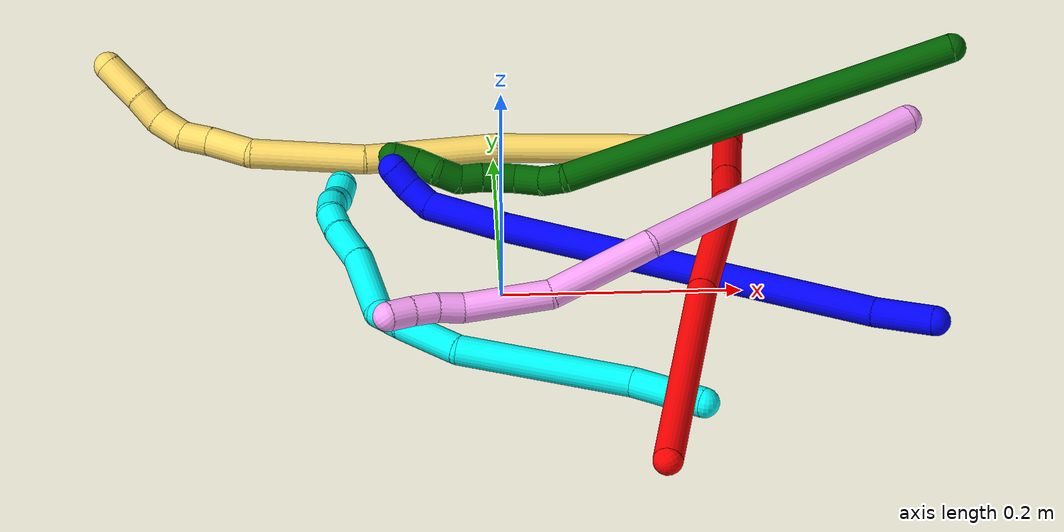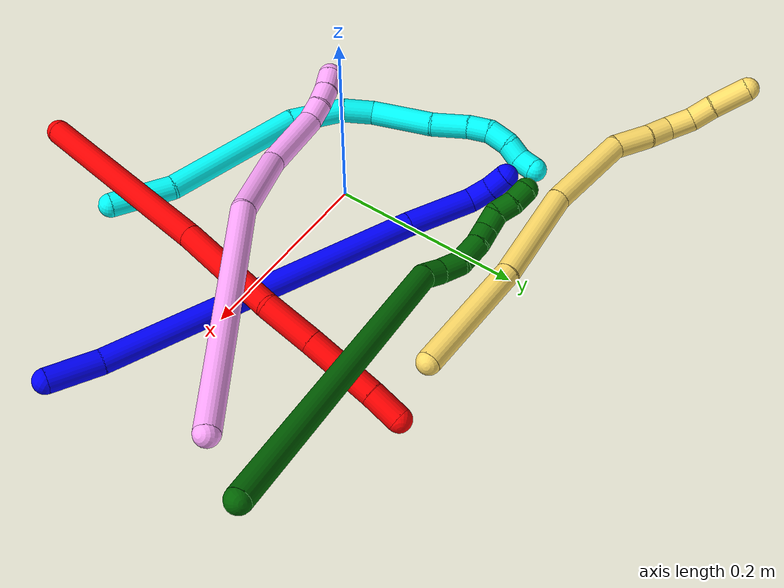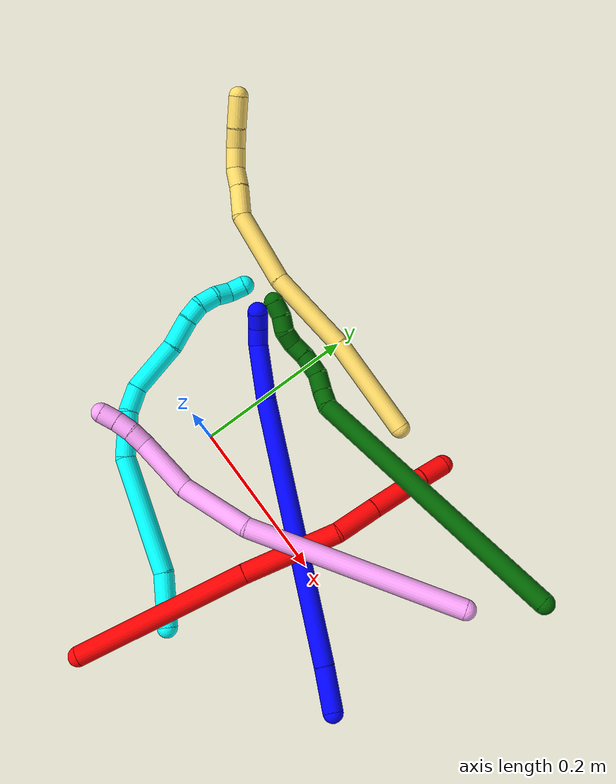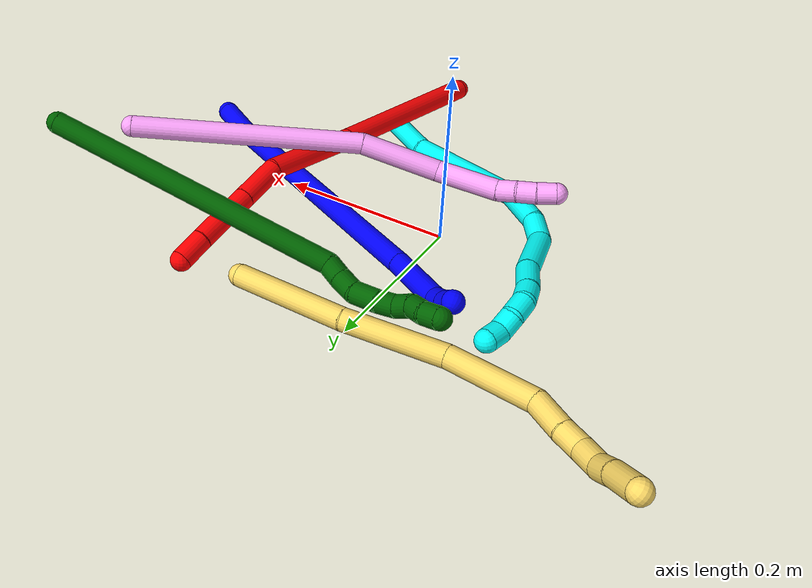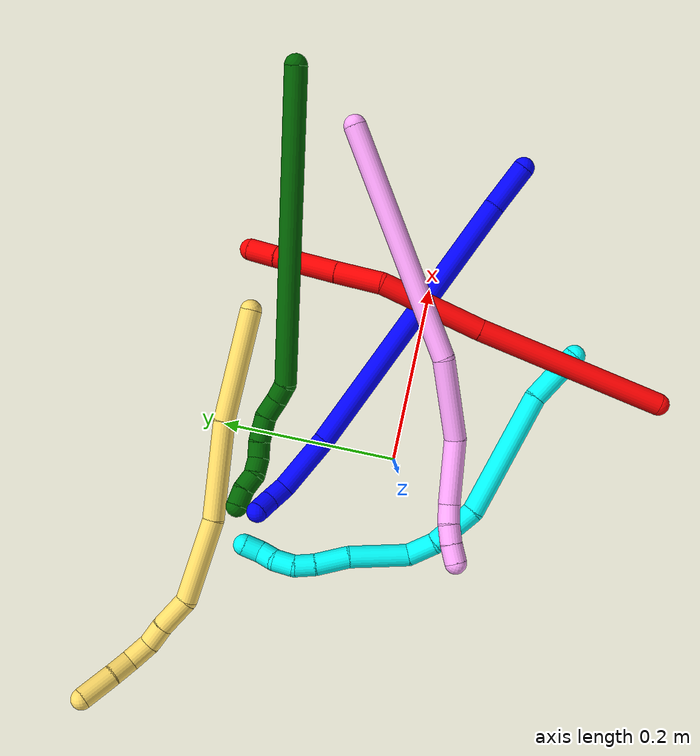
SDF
<sdf version="1.7">
 <world name="default">
  <plugin name="TubeGeneratorPlugin" filename="libtube_generator_plugin.so"/>
  <model name="photoneo_s_sensor">
   <static>1</static>
   <pose>0 0 2 1.57079 1.57079 3.14159</pose>
   <link name="link">
    <inertial><mass>0.1</mass></inertial>
    <sensor name="sensor" type="depth">
     <update_rate>30</update_rate>
     <camera>
      <horizontal_fov>1.22</horizontal_fov>
      <image><width>1920</width><height>1200</height><format>B8G8R8</format></image>
      <clip><near>0.1</near><far>4</far></clip>
      <depth_camera><output>points</output></depth_camera>
     </camera>
     <plugin name="camera_plugin" filename="libgazebo_ros_depth_camera.so">
      <baseline>0.2</baseline>
      <alwaysOn>1</alwaysOn>
      <updateRate>0.0</updateRate>
      <cameraName>camera_ir</cameraName>
      <imageTopicName>/camera/color/image_raw</imageTopicName>
      <cameraInfoTopicName>/camera/color/camera_info</cameraInfoTopicName>
      <depthImageTopicName>/camera/depth/image_raw</depthImageTopicName>
      <depthImageCameraInfoTopicName>/camera/depth/camera_info</depthImageCameraInfoTopicName>
      <pointCloudTopicName>/camera/depth/points</pointCloudTopicName>
      <frameName>fr_optical</frameName>
      <pointCloudCutoff>0.1</pointCloudCutoff>
      <pointCloudCutoffMax>2.0</pointCloudCutoffMax>
      <distortionK1>0</distortionK1>
      <distortionK2>0</distortionK2>
      <distortionK3>0</distortionK3>
      <distortionT1>0</distortionT1>
      <distortionT2>0</distortionT2>
      <CxPrime>0</CxPrime>
      <Cx>0</Cx>
      <Cy>0</Cy>
      <focalLength>0</focalLength>
      <hackBaseline>0</hackBaseline>
     </plugin>
    </sensor>
   </link>
  </model>
  <gravity>0 0 -9.8</gravity>
  <magnetic_field>6e-06 2.3e-05 -4.2e-05</magnetic_field>
  <atmosphere type="adiabatic"/>
  <physics name="default_physics" default="0" type="ode">
   <max_step_size>0.003</max_step_size>
   <real_time_factor>1</real_time_factor>
   <real_time_update_rate>1000</real_time_update_rate>
   <max_contacts>10000</max_contacts>
   <ode>
    <solver>
     <type>quick</type>
     <iters>100</iters>
     <sor>1.3</sor>
     <use_dynamic_moi_rescaling>0</use_dynamic_moi_rescaling>
    </solver>
    <constraints>
     <contact_max_correcting_vel>0</contact_max_correcting_vel>
     <contact_surface_layer>0.001</contact_surface_layer>
     <cfm>0</cfm>
     <erp>0.2</erp>
    </constraints>
   </ode>
  </physics>
  <scene><ambient>0.4 0.4 0.4 1</ambient><background>0.7 0.7 0.7 1</background><shadows>0</shadows></scene>
  <audio><device>default</device></audio>
  <spherical_coordinates>
   <surface_model>EARTH_WGS84</surface_model>
   <latitude_deg>0</latitude_deg>
   <longitude_deg>0</longitude_deg>
   <elevation>0</elevation>
   <heading_deg>0</heading_deg>
  </spherical_coordinates>
  <model name="bin">
   <static>1</static>
   <link name="bottom">
    <collision name="collision-bottom">
     <pose>0 0 -0.01 0 -0 0</pose>
     <geometry><box><size>0.8 0.6 0.02</size></box></geometry>
     <surface>
      <friction><ode><mu>100</mu><mu2>100</mu2></ode></friction>
      <contact><collide_bitmask>65535</collide_bitmask></contact>
     </surface>
    </collision>
   </link>
   <link name="west_wall">
    <collision name="collision-west_wall">
     <pose>-0.41 0 0.1 0 -0 0</pose>
     <geometry><box><size>0.02 0.6 0.2</size></box></geometry>
     <surface>
      <friction><ode><mu>100</mu><mu2>100</mu2></ode></friction>
      <contact><collide_bitmask>65535</collide_bitmask></contact>
     </surface>
    </collision>
   </link>
   <link name="east_wall">
    <collision name="collision-east_wall">
     <pose>0.41 0 0.1 0 -0 0</pose>
     <geometry><box><size>0.02 0.6 0.2</size></box></geometry>
     <surface>
      <friction><ode><mu>100</mu><mu2>100</mu2></ode></friction>
      <contact><collide_bitmask>65535</collide_bitmask></contact>
     </surface>
    </collision>
   </link>
   <link name="south_wall">
    <collision name="collision-south_wall">
     <pose>0 -0.31 0.1 0 -0 0</pose>
     <geometry><box><size>0.8 0.02 0.2</size></box></geometry>
     <surface>
      <friction><ode><mu>100</mu><mu2>100</mu2></ode></friction>
      <contact><collide_bitmask>65535</collide_bitmask></contact>
     </surface>
    </collision>
   </link>
   <link name="north_wall">
    <collision name="collision-north_wall">
     <pose>0 0.31 0.1 0 -0 0</pose>
     <geometry><box><size>0.8 0.02 0.2</size></box></geometry>
     <surface>
      <friction><ode><mu>100</mu><mu2>100</mu2></ode></friction>
      <contact><collide_bitmask>65535</collide_bitmask></contact>
     </surface>
    </collision>
   </link>
  </model>
  <model name="1">
   <static>0</static>
   <link name="1">
    <collision name="collision-cylinder-e_1_1_4">
     <pose>-0.020728 -0.006324 -0.016088 2.76704 -0.87568 -2.37235</pose>
     <geometry><cylinder><radius>0.0125</radius><length>0.05398</length></cylinder></geometry>
     <surface>
      <friction><ode><mu>1.16</mu><mu2>1.16</mu2><slip1>0</slip1><slip2>0</slip2></ode></friction>
      <contact><ode><kp>1e+06</kp><kd>1</kd><max_vel>0</max_vel><min_depth>0.001</min_depth></ode></contact>
     </surface>
    </collision>
    <visual name="visual-cylinder-e_1_1_4">
     <pose>-0.020728 -0.006324 -0.016088 2.76704 -0.87568 -2.37235</pose>
     <geometry><cylinder><radius>0.0125</radius><length>0.05398</length></cylinder></geometry>
     <material><ambient>0 0 1 1</ambient></material>
    </visual>
    <collision name="collision-cylinder-e_2_4_5">
     <pose>-0.178863 -0.038031 -0.120422 2.86152 -0.98169 -2.62587</pose>
     <geometry><cylinder><radius>0.0125</radius><length>0.33053</length></cylinder></geometry>
     <surface>
      <friction><ode><mu>1.16</mu><mu2>1.16</mu2><slip1>0</slip1><slip2>0</slip2></ode></friction>
      <contact><ode><kp>1e+06</kp><kd>1</kd><max_vel>0</max_vel><min_depth>0.001</min_depth></ode></contact>
     </surface>
    </collision>
    <visual name="visual-cylinder-e_2_4_5">
     <pose>-0.178863 -0.038031 -0.120422 2.86152 -0.98169 -2.62587</pose>
     <geometry><cylinder><radius>0.0125</radius><length>0.33053</length></cylinder></geometry>
     <material><ambient>0 0 1 1</ambient></material>
    </visual>
    <collision name="collision-cylinder-e_3_5_6">
     <pose>-0.344973 -0.067262 -0.229293 2.95711 -0.939599 -2.78116</pose>
     <geometry><cylinder><radius>0.0125</radius><length>0.071106</length></cylinder></geometry>
     <surface>
      <friction><ode><mu>1.16</mu><mu2>1.16</mu2><slip1>0</slip1><slip2>0</slip2></ode></friction>
      <contact><ode><kp>1e+06</kp><kd>1</kd><max_vel>0</max_vel><min_depth>0.001</min_depth></ode></contact>
     </surface>
    </collision>
    <visual name="visual-cylinder-e_3_5_6">
     <pose>-0.344973 -0.067262 -0.229293 2.95711 -0.939599 -2.78116</pose>
     <geometry><cylinder><radius>0.0125</radius><length>0.071106</length></cylinder></geometry>
     <material><ambient>0 0 1 1</ambient></material>
    </visual>
    <collision name="collision-cylinder-e_4_6_7">
     <pose>-0.383408 -0.067005 -0.255105 -2.47216 -0.973713 1.97899</pose>
     <geometry><cylinder><radius>0.0125</radius><length>0.023536</length></cylinder></geometry>
     <surface>
      <friction><ode><mu>1.16</mu><mu2>1.16</mu2><slip1>0</slip1><slip2>0</slip2></ode></friction>
      <contact><ode><kp>1e+06</kp><kd>1</kd><max_vel>0</max_vel><min_depth>0.001</min_depth></ode></contact>
     </surface>
    </collision>
    <visual name="visual-cylinder-e_4_6_7">
     <pose>-0.383408 -0.067005 -0.255105 -2.47216 -0.973713 1.97899</pose>
     <geometry><cylinder><radius>0.0125</radius><length>0.023536</length></cylinder></geometry>
     <material><ambient>0 0 1 1</ambient></material>
    </visual>
    <collision name="collision-cylinder-e_5_7_2">
     <pose>-0.401753 -0.057852 -0.263295 -2.10717 -0.972416 1.49732</pose>
     <geometry><cylinder><radius>0.0125</radius><length>0.020848</length></cylinder></geometry>
     <surface>
      <friction><ode><mu>1.16</mu><mu2>1.16</mu2><slip1>0</slip1><slip2>0</slip2></ode></friction>
      <contact><ode><kp>1e+06</kp><kd>1</kd><max_vel>0</max_vel><min_depth>0.001</min_depth></ode></contact>
     </surface>
    </collision>
    <visual name="visual-cylinder-e_5_7_2">
     <pose>-0.401753 -0.057852 -0.263295 -2.10717 -0.972416 1.49732</pose>
     <geometry><cylinder><radius>0.0125</radius><length>0.020848</length></cylinder></geometry>
     <material><ambient>0 0 1 1</ambient></material>
    </visual>
    <collision name="collision-sphere-2">
     <pose>-0.410365 -0.052805 -0.266295 0 -0 0</pose>
     <geometry><sphere><radius>0.0125</radius></sphere></geometry>
     <surface>
      <friction><ode><mu>1.16</mu><mu2>1.16</mu2><slip1>0</slip1><slip2>0</slip2></ode></friction>
      <contact><ode><kp>1e+06</kp><kd>1</kd><max_vel>0</max_vel><min_depth>0.001</min_depth></ode></contact>
     </surface>
    </collision>
    <visual name="visual-sphere-2">
     <pose>-0.410365 -0.052805 -0.266295 0 -0 0</pose>
     <geometry><sphere><radius>0.0125</radius></sphere></geometry>
     <material><ambient>0 0 1 1</ambient></material>
    </visual>
    <collision name="collision-sphere-7">
     <pose>-0.39314 -0.062899 -0.260294 0 -0 0</pose>
     <geometry><sphere><radius>0.0125</radius></sphere></geometry>
     <surface>
      <friction><ode><mu>1.16</mu><mu2>1.16</mu2><slip1>0</slip1><slip2>0</slip2></ode></friction>
      <contact><ode><kp>1e+06</kp><kd>1</kd><max_vel>0</max_vel><min_depth>0.001</min_depth></ode></contact>
     </surface>
    </collision>
    <visual name="visual-sphere-7">
     <pose>-0.39314 -0.062899 -0.260294 0 -0 0</pose>
     <geometry><sphere><radius>0.0125</radius></sphere></geometry>
     <material><ambient>0 0 1 1</ambient></material>
    </visual>
    <collision name="collision-sphere-6">
     <pose>-0.373676 -0.071111 -0.249917 0 -0 0</pose>
     <geometry><sphere><radius>0.0125</radius></sphere></geometry>
     <surface>
      <friction><ode><mu>1.16</mu><mu2>1.16</mu2><slip1>0</slip1><slip2>0</slip2></ode></friction>
      <contact><ode><kp>1e+06</kp><kd>1</kd><max_vel>0</max_vel><min_depth>0.001</min_depth></ode></contact>
     </surface>
    </collision>
    <visual name="visual-sphere-6">
     <pose>-0.373676 -0.071111 -0.249917 0 -0 0</pose>
     <geometry><sphere><radius>0.0125</radius></sphere></geometry>
     <material><ambient>0 0 1 1</ambient></material>
    </visual>
    <collision name="collision-sphere-5">
     <pose>-0.31627 -0.063414 -0.208668 0 -0 0</pose>
     <geometry><sphere><radius>0.0125</radius></sphere></geometry>
     <surface>
      <friction><ode><mu>1.16</mu><mu2>1.16</mu2><slip1>0</slip1><slip2>0</slip2></ode></friction>
      <contact><ode><kp>1e+06</kp><kd>1</kd><max_vel>0</max_vel><min_depth>0.001</min_depth></ode></contact>
     </surface>
    </collision>
    <visual name="visual-sphere-5">
     <pose>-0.31627 -0.063414 -0.208668 0 -0 0</pose>
     <geometry><sphere><radius>0.0125</radius></sphere></geometry>
     <material><ambient>0 0 1 1</ambient></material>
    </visual>
    <collision name="collision-sphere-1">
     <geometry><sphere><radius>0.0125</radius></sphere></geometry>
     <surface>
      <friction><ode><mu>1.16</mu><mu2>1.16</mu2><slip1>0</slip1><slip2>0</slip2></ode></friction>
      <contact><ode><kp>1e+06</kp><kd>1</kd><max_vel>0</max_vel><min_depth>0.001</min_depth></ode></contact>
     </surface>
    </collision>
    <visual name="visual-sphere-1">
     <geometry><sphere><radius>0.0125</radius></sphere></geometry>
     <material><ambient>0 0 1 1</ambient></material>
    </visual>
    <collision name="collision-sphere-4">
     <pose>-0.041455 -0.012649 -0.032176 0 -0 0</pose>
     <geometry><sphere><radius>0.0125</radius></sphere></geometry>
     <surface>
      <friction><ode><mu>1.16</mu><mu2>1.16</mu2><slip1>0</slip1><slip2>0</slip2></ode></friction>
      <contact><ode><kp>1e+06</kp><kd>1</kd><max_vel>0</max_vel><min_depth>0.001</min_depth></ode></contact>
     </surface>
    </collision>
    <visual name="visual-sphere-4">
     <pose>-0.041455 -0.012649 -0.032176 0 -0 0</pose>
     <geometry><sphere><radius>0.0125</radius></sphere></geometry>
     <material><ambient>0 0 1 1</ambient></material>
    </visual>
    <inertial>
     <pose>-0.204336 -0.040956 -0.136938 0 -0 0</pose>
     <mass>0.5</mass>
     <inertia>
      <ixx>-0.002358</ixx>
      <ixy>0</ixy>
      <ixz>0</ixz>
      <iyy>0.002073</iyy>
      <iyz>0</iyz>
      <izz>0.003003</izz>
     </inertia>
    </inertial>
   </link>
   <pose>0.356163 -0.07522 0.017799 1.12849 0.41604 0.010042</pose>
  </model>
  <model name="2">
   <static>0</static>
   <link name="2">
    <collision name="collision-cylinder-e_1_1_4">
     <pose>0.038939 0.051101 -0.088487 -2.61788 0.364083 -1.20368</pose>
     <geometry><cylinder><radius>0.0125</radius><length>0.218701</length></cylinder></geometry>
     <surface>
      <friction><ode><mu>1.16</mu><mu2>1.16</mu2><slip1>0</slip1><slip2>0</slip2></ode></friction>
      <contact><ode><kp>1e+06</kp><kd>1</kd><max_vel>0</max_vel><min_depth>0.001</min_depth></ode></contact>
     </surface>
    </collision>
    <visual name="visual-cylinder-e_1_1_4">
     <pose>0.038939 0.051101 -0.088487 -2.61788 0.364083 -1.20368</pose>
     <geometry><cylinder><radius>0.0125</radius><length>0.218701</length></cylinder></geometry>
     <material><ambient>1 0 0 1</ambient></material>
    </visual>
    <collision name="collision-cylinder-e_2_4_5">
     <pose>0.097325 0.128733 -0.227298 -2.65642 0.329394 -1.18287</pose>
     <geometry><cylinder><radius>0.0125</radius><length>0.120242</length></cylinder></geometry>
     <surface>
      <friction><ode><mu>1.16</mu><mu2>1.16</mu2><slip1>0</slip1><slip2>0</slip2></ode></friction>
      <contact><ode><kp>1e+06</kp><kd>1</kd><max_vel>0</max_vel><min_depth>0.001</min_depth></ode></contact>
     </surface>
    </collision>
    <visual name="visual-cylinder-e_2_4_5">
     <pose>0.097325 0.128733 -0.227298 -2.65642 0.329394 -1.18287</pose>
     <geometry><cylinder><radius>0.0125</radius><length>0.120242</length></cylinder></geometry>
     <material><ambient>1 0 0 1</ambient></material>
    </visual>
    <collision name="collision-cylinder-e_3_5_6">
     <pose>0.121944 0.174062 -0.29617 -2.34949 0.193381 -0.455855</pose>
     <geometry><cylinder><radius>0.0125</radius><length>0.053822</length></cylinder></geometry>
     <surface>
      <friction><ode><mu>1.16</mu><mu2>1.16</mu2><slip1>0</slip1><slip2>0</slip2></ode></friction>
      <contact><ode><kp>1e+06</kp><kd>1</kd><max_vel>0</max_vel><min_depth>0.001</min_depth></ode></contact>
     </surface>
    </collision>
    <visual name="visual-cylinder-e_3_5_6">
     <pose>0.121944 0.174062 -0.29617 -2.34949 0.193381 -0.455855</pose>
     <geometry><cylinder><radius>0.0125</radius><length>0.053822</length></cylinder></geometry>
     <material><ambient>1 0 0 1</ambient></material>
    </visual>
    <collision name="collision-cylinder-e_4_6_7">
     <pose>0.133138 0.218539 -0.34037 -2.35569 0.164421 -0.392447</pose>
     <geometry><cylinder><radius>0.0125</radius><length>0.073582</length></cylinder></geometry>
     <surface>
      <friction><ode><mu>1.16</mu><mu2>1.16</mu2><slip1>0</slip1><slip2>0</slip2></ode></friction>
      <contact><ode><kp>1e+06</kp><kd>1</kd><max_vel>0</max_vel><min_depth>0.001</min_depth></ode></contact>
     </surface>
    </collision>
    <visual name="visual-cylinder-e_4_6_7">
     <pose>0.133138 0.218539 -0.34037 -2.35569 0.164421 -0.392447</pose>
     <geometry><cylinder><radius>0.0125</radius><length>0.073582</length></cylinder></geometry>
     <material><ambient>1 0 0 1</ambient></material>
    </visual>
    <collision name="collision-cylinder-e_5_7_2">
     <pose>0.140852 0.256174 -0.377738 -2.34601 0.100721 -0.238765</pose>
     <geometry><cylinder><radius>0.0125</radius><length>0.033653</length></cylinder></geometry>
     <surface>
      <friction><ode><mu>1.16</mu><mu2>1.16</mu2><slip1>0</slip1><slip2>0</slip2></ode></friction>
      <contact><ode><kp>1e+06</kp><kd>1</kd><max_vel>0</max_vel><min_depth>0.001</min_depth></ode></contact>
     </surface>
    </collision>
    <visual name="visual-cylinder-e_5_7_2">
     <pose>0.140852 0.256174 -0.377738 -2.34601 0.100721 -0.238765</pose>
     <geometry><cylinder><radius>0.0125</radius><length>0.033653</length></cylinder></geometry>
     <material><ambient>1 0 0 1</ambient></material>
    </visual>
    <collision name="collision-sphere-2">
     <pose>0.142544 0.268131 -0.389455 0 -0 0</pose>
     <geometry><sphere><radius>0.0125</radius></sphere></geometry>
     <surface>
      <friction><ode><mu>1.16</mu><mu2>1.16</mu2><slip1>0</slip1><slip2>0</slip2></ode></friction>
      <contact><ode><kp>1e+06</kp><kd>1</kd><max_vel>0</max_vel><min_depth>0.001</min_depth></ode></contact>
     </surface>
    </collision>
    <visual name="visual-sphere-2">
     <pose>0.142544 0.268131 -0.389455 0 -0 0</pose>
     <geometry><sphere><radius>0.0125</radius></sphere></geometry>
     <material><ambient>1 0 0 1</ambient></material>
    </visual>
    <collision name="collision-sphere-7">
     <pose>0.13916 0.244216 -0.366021 0 -0 0</pose>
     <geometry><sphere><radius>0.0125</radius></sphere></geometry>
     <surface>
      <friction><ode><mu>1.16</mu><mu2>1.16</mu2><slip1>0</slip1><slip2>0</slip2></ode></friction>
      <contact><ode><kp>1e+06</kp><kd>1</kd><max_vel>0</max_vel><min_depth>0.001</min_depth></ode></contact>
     </surface>
    </collision>
    <visual name="visual-sphere-7">
     <pose>0.13916 0.244216 -0.366021 0 -0 0</pose>
     <geometry><sphere><radius>0.0125</radius></sphere></geometry>
     <material><ambient>1 0 0 1</ambient></material>
    </visual>
    <collision name="collision-sphere-6">
     <pose>0.127116 0.192862 -0.314719 0 -0 0</pose>
     <geometry><sphere><radius>0.0125</radius></sphere></geometry>
     <surface>
      <friction><ode><mu>1.16</mu><mu2>1.16</mu2><slip1>0</slip1><slip2>0</slip2></ode></friction>
      <contact><ode><kp>1e+06</kp><kd>1</kd><max_vel>0</max_vel><min_depth>0.001</min_depth></ode></contact>
     </surface>
    </collision>
    <visual name="visual-sphere-6">
     <pose>0.127116 0.192862 -0.314719 0 -0 0</pose>
     <geometry><sphere><radius>0.0125</radius></sphere></geometry>
     <material><ambient>1 0 0 1</ambient></material>
    </visual>
    <collision name="collision-sphere-5">
     <pose>0.116773 0.155263 -0.277622 0 -0 0</pose>
     <geometry><sphere><radius>0.0125</radius></sphere></geometry>
     <surface>
      <friction><ode><mu>1.16</mu><mu2>1.16</mu2><slip1>0</slip1><slip2>0</slip2></ode></friction>
      <contact><ode><kp>1e+06</kp><kd>1</kd><max_vel>0</max_vel><min_depth>0.001</min_depth></ode></contact>
     </surface>
    </collision>
    <visual name="visual-sphere-5">
     <pose>0.116773 0.155263 -0.277622 0 -0 0</pose>
     <geometry><sphere><radius>0.0125</radius></sphere></geometry>
     <material><ambient>1 0 0 1</ambient></material>
    </visual>
    <collision name="collision-sphere-1">
     <geometry><sphere><radius>0.0125</radius></sphere></geometry>
     <surface>
      <friction><ode><mu>1.16</mu><mu2>1.16</mu2><slip1>0</slip1><slip2>0</slip2></ode></friction>
      <contact><ode><kp>1e+06</kp><kd>1</kd><max_vel>0</max_vel><min_depth>0.001</min_depth></ode></contact>
     </surface>
    </collision>
    <visual name="visual-sphere-1">
     <geometry><sphere><radius>0.0125</radius></sphere></geometry>
     <material><ambient>1 0 0 1</ambient></material>
    </visual>
    <collision name="collision-sphere-4">
     <pose>0.077878 0.102202 -0.176975 0 -0 0</pose>
     <geometry><sphere><radius>0.0125</radius></sphere></geometry>
     <surface>
      <friction><ode><mu>1.16</mu><mu2>1.16</mu2><slip1>0</slip1><slip2>0</slip2></ode></friction>
      <contact><ode><kp>1e+06</kp><kd>1</kd><max_vel>0</max_vel><min_depth>0.001</min_depth></ode></contact>
     </surface>
    </collision>
    <visual name="visual-sphere-4">
     <pose>0.077878 0.102202 -0.176975 0 -0 0</pose>
     <geometry><sphere><radius>0.0125</radius></sphere></geometry>
     <material><ambient>1 0 0 1</ambient></material>
    </visual>
    <inertial>
     <pose>0.082637 0.12145 -0.200761 0 -0 0</pose>
     <mass>0.5</mass>
     <inertia>
      <ixx>-0.00051</ixx>
      <ixy>0</ixy>
      <ixz>0</ixz>
      <iyy>-0.001089</iyy>
      <iyz>0</iyz>
      <izz>-0.000918</izz>
     </inertia>
    </inertial>
   </link>
   <pose>0.124067 -0.277333 0.031082 -1.70115 -0.913818 2.43451</pose>
  </model>
  <model name="3">
   <static>0</static>
   <link name="3">
    <collision name="collision-cylinder-e_1_1_4">
     <pose>-0.029544 0.013984 -0.001623 -1.68633 -1.12612 1.2331</pose>
     <geometry><cylinder><radius>0.0125</radius><length>0.065453</length></cylinder></geometry>
     <surface>
      <friction><ode><mu>1.16</mu><mu2>1.16</mu2><slip1>0</slip1><slip2>0</slip2></ode></friction>
      <contact><ode><kp>1e+06</kp><kd>1</kd><max_vel>0</max_vel><min_depth>0.001</min_depth></ode></contact>
     </surface>
    </collision>
    <visual name="visual-cylinder-e_1_1_4">
     <pose>-0.029544 0.013984 -0.001623 -1.68633 -1.12612 1.2331</pose>
     <geometry><cylinder><radius>0.0125</radius><length>0.065453</length></cylinder></geometry>
     <material><ambient>0.003922 1 0.996078 1</ambient></material>
    </visual>
    <collision name="collision-cylinder-e_2_4_5">
     <pose>-0.131987 0.041606 -0.005925 -1.76474 -1.38239 1.57644</pose>
     <geometry><cylinder><radius>0.0125</radius><length>0.148423</length></cylinder></geometry>
     <surface>
      <friction><ode><mu>1.16</mu><mu2>1.16</mu2><slip1>0</slip1><slip2>0</slip2></ode></friction>
      <contact><ode><kp>1e+06</kp><kd>1</kd><max_vel>0</max_vel><min_depth>0.001</min_depth></ode></contact>
     </surface>
    </collision>
    <visual name="visual-cylinder-e_2_4_5">
     <pose>-0.131987 0.041606 -0.005925 -1.76474 -1.38239 1.57644</pose>
     <geometry><cylinder><radius>0.0125</radius><length>0.148423</length></cylinder></geometry>
     <material><ambient>0.003922 1 0.996078 1</ambient></material>
    </visual>
    <collision name="collision-cylinder-e_3_5_6">
     <pose>-0.228911 0.07027 -0.007842 -1.52019 -1.01135 0.969032</pose>
     <geometry><cylinder><radius>0.0125</radius><length>0.056694</length></cylinder></geometry>
     <surface>
      <friction><ode><mu>1.16</mu><mu2>1.16</mu2><slip1>0</slip1><slip2>0</slip2></ode></friction>
      <contact><ode><kp>1e+06</kp><kd>1</kd><max_vel>0</max_vel><min_depth>0.001</min_depth></ode></contact>
     </surface>
    </collision>
    <visual name="visual-cylinder-e_3_5_6">
     <pose>-0.228911 0.07027 -0.007842 -1.52019 -1.01135 0.969032</pose>
     <geometry><cylinder><radius>0.0125</radius><length>0.056694</length></cylinder></geometry>
     <material><ambient>0.003922 1 0.996078 1</ambient></material>
    </visual>
    <collision name="collision-cylinder-e_4_6_7">
     <pose>-0.264044 0.097573 -0.008311 -1.67057 -0.732911 0.802263</pose>
     <geometry><cylinder><radius>0.0125</radius><length>0.033204</length></cylinder></geometry>
     <surface>
      <friction><ode><mu>1.16</mu><mu2>1.16</mu2><slip1>0</slip1><slip2>0</slip2></ode></friction>
      <contact><ode><kp>1e+06</kp><kd>1</kd><max_vel>0</max_vel><min_depth>0.001</min_depth></ode></contact>
     </surface>
    </collision>
    <visual name="visual-cylinder-e_4_6_7">
     <pose>-0.264044 0.097573 -0.008311 -1.67057 -0.732911 0.802263</pose>
     <geometry><cylinder><radius>0.0125</radius><length>0.033204</length></cylinder></geometry>
     <material><ambient>0.003922 1 0.996078 1</ambient></material>
    </visual>
    <collision name="collision-cylinder-e_5_7_8">
     <pose>-0.287047 0.140727 -0.000364 -1.28193 -0.353762 0.265146</pose>
     <geometry><cylinder><radius>0.0125</radius><length>0.068676</length></cylinder></geometry>
     <surface>
      <friction><ode><mu>1.16</mu><mu2>1.16</mu2><slip1>0</slip1><slip2>0</slip2></ode></friction>
      <contact><ode><kp>1e+06</kp><kd>1</kd><max_vel>0</max_vel><min_depth>0.001</min_depth></ode></contact>
     </surface>
    </collision>
    <visual name="visual-cylinder-e_5_7_8">
     <pose>-0.287047 0.140727 -0.000364 -1.28193 -0.353762 0.265146</pose>
     <geometry><cylinder><radius>0.0125</radius><length>0.068676</length></cylinder></geometry>
     <material><ambient>0.003922 1 0.996078 1</ambient></material>
    </visual>
    <collision name="collision-cylinder-e_6_8_9">
     <pose>-0.309072 0.187664 0.012919 -1.32044 -0.548525 0.430156</pose>
     <geometry><cylinder><radius>0.0125</radius><length>0.038853</length></cylinder></geometry>
     <surface>
      <friction><ode><mu>1.16</mu><mu2>1.16</mu2><slip1>0</slip1><slip2>0</slip2></ode></friction>
      <contact><ode><kp>1e+06</kp><kd>1</kd><max_vel>0</max_vel><min_depth>0.001</min_depth></ode></contact>
     </surface>
    </collision>
    <visual name="visual-cylinder-e_6_8_9">
     <pose>-0.309072 0.187664 0.012919 -1.32044 -0.548525 0.430156</pose>
     <geometry><cylinder><radius>0.0125</radius><length>0.038853</length></cylinder></geometry>
     <material><ambient>0.003922 1 0.996078 1</ambient></material>
    </visual>
    <collision name="collision-cylinder-e_7_9_10">
     <pose>-0.323626 0.214311 0.019481 -1.34292 -0.386675 0.308677</pose>
     <geometry><cylinder><radius>0.0125</radius><length>0.023469</length></cylinder></geometry>
     <surface>
      <friction><ode><mu>1.16</mu><mu2>1.16</mu2><slip1>0</slip1><slip2>0</slip2></ode></friction>
      <contact><ode><kp>1e+06</kp><kd>1</kd><max_vel>0</max_vel><min_depth>0.001</min_depth></ode></contact>
     </surface>
    </collision>
    <visual name="visual-cylinder-e_7_9_10">
     <pose>-0.323626 0.214311 0.019481 -1.34292 -0.386675 0.308677</pose>
     <geometry><cylinder><radius>0.0125</radius><length>0.023469</length></cylinder></geometry>
     <material><ambient>0.003922 1 0.996078 1</ambient></material>
    </visual>
    <collision name="collision-cylinder-e_8_10_11">
     <pose>-0.328633 0.236739 0.022298 -1.54029 -0.049086 0.047612</pose>
     <geometry><cylinder><radius>0.0125</radius><length>0.023723</length></cylinder></geometry>
     <surface>
      <friction><ode><mu>1.16</mu><mu2>1.16</mu2><slip1>0</slip1><slip2>0</slip2></ode></friction>
      <contact><ode><kp>1e+06</kp><kd>1</kd><max_vel>0</max_vel><min_depth>0.001</min_depth></ode></contact>
     </surface>
    </collision>
    <visual name="visual-cylinder-e_8_10_11">
     <pose>-0.328633 0.236739 0.022298 -1.54029 -0.049086 0.047612</pose>
     <geometry><cylinder><radius>0.0125</radius><length>0.023723</length></cylinder></geometry>
     <material><ambient>0.003922 1 0.996078 1</ambient></material>
    </visual>
    <collision name="collision-cylinder-e_9_11_12">
     <pose>-0.327684 0.258291 0.020168 -1.82192 0.151572 -0.195117</pose>
     <geometry><cylinder><radius>0.0125</radius><length>0.020281</length></cylinder></geometry>
     <surface>
      <friction><ode><mu>1.16</mu><mu2>1.16</mu2><slip1>0</slip1><slip2>0</slip2></ode></friction>
      <contact><ode><kp>1e+06</kp><kd>1</kd><max_vel>0</max_vel><min_depth>0.001</min_depth></ode></contact>
     </surface>
    </collision>
    <visual name="visual-cylinder-e_9_11_12">
     <pose>-0.327684 0.258291 0.020168 -1.82192 0.151572 -0.195117</pose>
     <geometry><cylinder><radius>0.0125</radius><length>0.020281</length></cylinder></geometry>
     <material><ambient>0.003922 1 0.996078 1</ambient></material>
    </visual>
    <collision name="collision-cylinder-e_10_12_2">
     <pose>-0.325337 0.278245 0.020325 -1.31783 0.076976 -0.059619</pose>
     <geometry><cylinder><radius>0.0125</radius><length>0.021224</length></cylinder></geometry>
     <surface>
      <friction><ode><mu>1.16</mu><mu2>1.16</mu2><slip1>0</slip1><slip2>0</slip2></ode></friction>
      <contact><ode><kp>1e+06</kp><kd>1</kd><max_vel>0</max_vel><min_depth>0.001</min_depth></ode></contact>
     </surface>
    </collision>
    <visual name="visual-cylinder-e_10_12_2">
     <pose>-0.325337 0.278245 0.020325 -1.31783 0.076976 -0.059619</pose>
     <geometry><cylinder><radius>0.0125</radius><length>0.021224</length></cylinder></geometry>
     <material><ambient>0.003922 1 0.996078 1</ambient></material>
    </visual>
    <collision name="collision-sphere-2">
     <pose>-0.324521 0.288488 0.022973 0 -0 0</pose>
     <geometry><sphere><radius>0.0125</radius></sphere></geometry>
     <surface>
      <friction><ode><mu>1.16</mu><mu2>1.16</mu2><slip1>0</slip1><slip2>0</slip2></ode></friction>
      <contact><ode><kp>1e+06</kp><kd>1</kd><max_vel>0</max_vel><min_depth>0.001</min_depth></ode></contact>
     </surface>
    </collision>
    <visual name="visual-sphere-2">
     <pose>-0.324521 0.288488 0.022973 0 -0 0</pose>
     <geometry><sphere><radius>0.0125</radius></sphere></geometry>
     <material><ambient>0.003922 1 0.996078 1</ambient></material>
    </visual>
    <collision name="collision-sphere-12">
     <pose>-0.326153 0.268001 0.017677 0 -0 0</pose>
     <geometry><sphere><radius>0.0125</radius></sphere></geometry>
     <surface>
      <friction><ode><mu>1.16</mu><mu2>1.16</mu2><slip1>0</slip1><slip2>0</slip2></ode></friction>
      <contact><ode><kp>1e+06</kp><kd>1</kd><max_vel>0</max_vel><min_depth>0.001</min_depth></ode></contact>
     </surface>
    </collision>
    <visual name="visual-sphere-12">
     <pose>-0.326153 0.268001 0.017677 0 -0 0</pose>
     <geometry><sphere><radius>0.0125</radius></sphere></geometry>
     <material><ambient>0.003922 1 0.996078 1</ambient></material>
    </visual>
    <collision name="collision-sphere-11">
     <pose>-0.329215 0.248581 0.022659 0 -0 0</pose>
     <geometry><sphere><radius>0.0125</radius></sphere></geometry>
     <surface>
      <friction><ode><mu>1.16</mu><mu2>1.16</mu2><slip1>0</slip1><slip2>0</slip2></ode></friction>
      <contact><ode><kp>1e+06</kp><kd>1</kd><max_vel>0</max_vel><min_depth>0.001</min_depth></ode></contact>
     </surface>
    </collision>
    <visual name="visual-sphere-11">
     <pose>-0.329215 0.248581 0.022659 0 -0 0</pose>
     <geometry><sphere><radius>0.0125</radius></sphere></geometry>
     <material><ambient>0.003922 1 0.996078 1</ambient></material>
    </visual>
    <collision name="collision-sphere-10">
     <pose>-0.328051 0.224898 0.021936 0 -0 0</pose>
     <geometry><sphere><radius>0.0125</radius></sphere></geometry>
     <surface>
      <friction><ode><mu>1.16</mu><mu2>1.16</mu2><slip1>0</slip1><slip2>0</slip2></ode></friction>
      <contact><ode><kp>1e+06</kp><kd>1</kd><max_vel>0</max_vel><min_depth>0.001</min_depth></ode></contact>
     </surface>
    </collision>
    <visual name="visual-sphere-10">
     <pose>-0.328051 0.224898 0.021936 0 -0 0</pose>
     <geometry><sphere><radius>0.0125</radius></sphere></geometry>
     <material><ambient>0.003922 1 0.996078 1</ambient></material>
    </visual>
    <collision name="collision-sphere-9">
     <pose>-0.319201 0.203724 0.017026 0 -0 0</pose>
     <geometry><sphere><radius>0.0125</radius></sphere></geometry>
     <surface>
      <friction><ode><mu>1.16</mu><mu2>1.16</mu2><slip1>0</slip1><slip2>0</slip2></ode></friction>
      <contact><ode><kp>1e+06</kp><kd>1</kd><max_vel>0</max_vel><min_depth>0.001</min_depth></ode></contact>
     </surface>
    </collision>
    <visual name="visual-sphere-9">
     <pose>-0.319201 0.203724 0.017026 0 -0 0</pose>
     <geometry><sphere><radius>0.0125</radius></sphere></geometry>
     <material><ambient>0.003922 1 0.996078 1</ambient></material>
    </visual>
    <collision name="collision-sphere-4">
     <pose>-0.059088 0.027968 -0.003246 0 -0 0</pose>
     <geometry><sphere><radius>0.0125</radius></sphere></geometry>
     <surface>
      <friction><ode><mu>1.16</mu><mu2>1.16</mu2><slip1>0</slip1><slip2>0</slip2></ode></friction>
      <contact><ode><kp>1e+06</kp><kd>1</kd><max_vel>0</max_vel><min_depth>0.001</min_depth></ode></contact>
     </surface>
    </collision>
    <visual name="visual-sphere-4">
     <pose>-0.059088 0.027968 -0.003246 0 -0 0</pose>
     <geometry><sphere><radius>0.0125</radius></sphere></geometry>
     <material><ambient>0.003922 1 0.996078 1</ambient></material>
    </visual>
    <collision name="collision-sphere-1">
     <geometry><sphere><radius>0.0125</radius></sphere></geometry>
     <surface>
      <friction><ode><mu>1.16</mu><mu2>1.16</mu2><slip1>0</slip1><slip2>0</slip2></ode></friction>
      <contact><ode><kp>1e+06</kp><kd>1</kd><max_vel>0</max_vel><min_depth>0.001</min_depth></ode></contact>
     </surface>
    </collision>
    <visual name="visual-sphere-1">
     <geometry><sphere><radius>0.0125</radius></sphere></geometry>
     <material><ambient>0.003922 1 0.996078 1</ambient></material>
    </visual>
    <collision name="collision-sphere-8">
     <pose>-0.298942 0.171604 0.008812 0 -0 0</pose>
     <geometry><sphere><radius>0.0125</radius></sphere></geometry>
     <surface>
      <friction><ode><mu>1.16</mu><mu2>1.16</mu2><slip1>0</slip1><slip2>0</slip2></ode></friction>
      <contact><ode><kp>1e+06</kp><kd>1</kd><max_vel>0</max_vel><min_depth>0.001</min_depth></ode></contact>
     </surface>
    </collision>
    <visual name="visual-sphere-8">
     <pose>-0.298942 0.171604 0.008812 0 -0 0</pose>
     <geometry><sphere><radius>0.0125</radius></sphere></geometry>
     <material><ambient>0.003922 1 0.996078 1</ambient></material>
    </visual>
    <collision name="collision-sphere-5">
     <pose>-0.204885 0.055245 -0.008603 0 -0 0</pose>
     <geometry><sphere><radius>0.0125</radius></sphere></geometry>
     <surface>
      <friction><ode><mu>1.16</mu><mu2>1.16</mu2><slip1>0</slip1><slip2>0</slip2></ode></friction>
      <contact><ode><kp>1e+06</kp><kd>1</kd><max_vel>0</max_vel><min_depth>0.001</min_depth></ode></contact>
     </surface>
    </collision>
    <visual name="visual-sphere-5">
     <pose>-0.204885 0.055245 -0.008603 0 -0 0</pose>
     <geometry><sphere><radius>0.0125</radius></sphere></geometry>
     <material><ambient>0.003922 1 0.996078 1</ambient></material>
    </visual>
    <collision name="collision-sphere-6">
     <pose>-0.252936 0.085295 -0.007082 0 -0 0</pose>
     <geometry><sphere><radius>0.0125</radius></sphere></geometry>
     <surface>
      <friction><ode><mu>1.16</mu><mu2>1.16</mu2><slip1>0</slip1><slip2>0</slip2></ode></friction>
      <contact><ode><kp>1e+06</kp><kd>1</kd><max_vel>0</max_vel><min_depth>0.001</min_depth></ode></contact>
     </surface>
    </collision>
    <visual name="visual-sphere-6">
     <pose>-0.252936 0.085295 -0.007082 0 -0 0</pose>
     <geometry><sphere><radius>0.0125</radius></sphere></geometry>
     <material><ambient>0.003922 1 0.996078 1</ambient></material>
    </visual>
    <collision name="collision-sphere-7">
     <pose>-0.275151 0.10985 -0.00954 0 -0 0</pose>
     <geometry><sphere><radius>0.0125</radius></sphere></geometry>
     <surface>
      <friction><ode><mu>1.16</mu><mu2>1.16</mu2><slip1>0</slip1><slip2>0</slip2></ode></friction>
      <contact><ode><kp>1e+06</kp><kd>1</kd><max_vel>0</max_vel><min_depth>0.001</min_depth></ode></contact>
     </surface>
    </collision>
    <visual name="visual-sphere-7">
     <pose>-0.275151 0.10985 -0.00954 0 -0 0</pose>
     <geometry><sphere><radius>0.0125</radius></sphere></geometry>
     <material><ambient>0.003922 1 0.996078 1</ambient></material>
    </visual>
    <inertial>
     <pose>-0.207864 0.10612 0.001195 0 -0 0</pose>
     <mass>0.5</mass>
     <inertia>
      <ixx>0.000107</ixx>
      <ixy>0</ixy>
      <ixz>0</ixz>
      <iyy>0.000423</iyy>
      <iyz>0</iyz>
      <izz>0.000217</izz>
     </inertia>
    </inertial>
   </link>
   <pose>0.159285 -0.176826 0.013719 -0.206729 0.110896 -0.120957</pose>
  </model>
  <model name="4">
   <static>0</static>
   <link name="4">
    <collision name="collision-cylinder-e_1_1_4">
     <pose>-0.104037 0.030611 -0.077881 -2.76709 -0.893415 2.38827</pose>
     <geometry><cylinder><radius>0.0125</radius><length>0.26703</length></cylinder></geometry>
     <surface>
      <friction><ode><mu>1.16</mu><mu2>1.16</mu2><slip1>0</slip1><slip2>0</slip2></ode></friction>
      <contact><ode><kp>1e+06</kp><kd>1</kd><max_vel>0</max_vel><min_depth>0.001</min_depth></ode></contact>
     </surface>
    </collision>
    <visual name="visual-cylinder-e_1_1_4">
     <pose>-0.104037 0.030611 -0.077881 -2.76709 -0.893415 2.38827</pose>
     <geometry><cylinder><radius>0.0125</radius><length>0.26703</length></cylinder></geometry>
     <material><ambient>1 0.65098 0.996078 1</ambient></material>
    </visual>
    <collision name="collision-cylinder-e_2_4_5">
     <pose>-0.235335 0.070746 -0.192328 -2.88678 -0.624996 2.38663</pose>
     <geometry><cylinder><radius>0.0125</radius><length>0.093186</length></cylinder></geometry>
     <surface>
      <friction><ode><mu>1.16</mu><mu2>1.16</mu2><slip1>0</slip1><slip2>0</slip2></ode></friction>
      <contact><ode><kp>1e+06</kp><kd>1</kd><max_vel>0</max_vel><min_depth>0.001</min_depth></ode></contact>
     </surface>
    </collision>
    <visual name="visual-cylinder-e_2_4_5">
     <pose>-0.235335 0.070746 -0.192328 -2.88678 -0.624996 2.38663</pose>
     <geometry><cylinder><radius>0.0125</radius><length>0.093186</length></cylinder></geometry>
     <material><ambient>1 0.65098 0.996078 1</ambient></material>
    </visual>
    <collision name="collision-cylinder-e_3_5_6">
     <pose>-0.279155 0.098255 -0.256555 -2.56512 -0.465123 1.34804</pose>
     <geometry><cylinder><radius>0.0125</radius><length>0.073834</length></cylinder></geometry>
     <surface>
      <friction><ode><mu>1.16</mu><mu2>1.16</mu2><slip1>0</slip1><slip2>0</slip2></ode></friction>
      <contact><ode><kp>1e+06</kp><kd>1</kd><max_vel>0</max_vel><min_depth>0.001</min_depth></ode></contact>
     </surface>
    </collision>
    <visual name="visual-cylinder-e_3_5_6">
     <pose>-0.279155 0.098255 -0.256555 -2.56512 -0.465123 1.34804</pose>
     <geometry><cylinder><radius>0.0125</radius><length>0.073834</length></cylinder></geometry>
     <material><ambient>1 0.65098 0.996078 1</ambient></material>
    </visual>
    <collision name="collision-cylinder-e_4_6_7">
     <pose>-0.301777 0.123282 -0.290404 -2.29153 -0.57422 1.15606</pose>
     <geometry><cylinder><radius>0.0125</radius><length>0.022328</length></cylinder></geometry>
     <surface>
      <friction><ode><mu>1.16</mu><mu2>1.16</mu2><slip1>0</slip1><slip2>0</slip2></ode></friction>
      <contact><ode><kp>1e+06</kp><kd>1</kd><max_vel>0</max_vel><min_depth>0.001</min_depth></ode></contact>
     </surface>
    </collision>
    <visual name="visual-cylinder-e_4_6_7">
     <pose>-0.301777 0.123282 -0.290404 -2.29153 -0.57422 1.15606</pose>
     <geometry><cylinder><radius>0.0125</radius><length>0.022328</length></cylinder></geometry>
     <material><ambient>1 0.65098 0.996078 1</ambient></material>
    </visual>
    <collision name="collision-cylinder-e_5_7_8">
     <pose>-0.314788 0.135666 -0.303068 -2.45216 -0.691225 1.57361</pose>
     <geometry><cylinder><radius>0.0125</radius><length>0.021794</length></cylinder></geometry>
     <surface>
      <friction><ode><mu>1.16</mu><mu2>1.16</mu2><slip1>0</slip1><slip2>0</slip2></ode></friction>
      <contact><ode><kp>1e+06</kp><kd>1</kd><max_vel>0</max_vel><min_depth>0.001</min_depth></ode></contact>
     </surface>
    </collision>
    <visual name="visual-cylinder-e_5_7_8">
     <pose>-0.314788 0.135666 -0.303068 -2.45216 -0.691225 1.57361</pose>
     <geometry><cylinder><radius>0.0125</radius><length>0.021794</length></cylinder></geometry>
     <material><ambient>1 0.65098 0.996078 1</ambient></material>
    </visual>
    <collision name="collision-cylinder-e_6_8_2">
     <pose>-0.329638 0.145672 -0.315454 -2.47316 -0.80971 1.77959</pose>
     <geometry><cylinder><radius>0.0125</radius><length>0.021828</length></cylinder></geometry>
     <surface>
      <friction><ode><mu>1.16</mu><mu2>1.16</mu2><slip1>0</slip1><slip2>0</slip2></ode></friction>
      <contact><ode><kp>1e+06</kp><kd>1</kd><max_vel>0</max_vel><min_depth>0.001</min_depth></ode></contact>
     </surface>
    </collision>
    <visual name="visual-cylinder-e_6_8_2">
     <pose>-0.329638 0.145672 -0.315454 -2.47316 -0.80971 1.77959</pose>
     <geometry><cylinder><radius>0.0125</radius><length>0.021828</length></cylinder></geometry>
     <material><ambient>1 0.65098 0.996078 1</ambient></material>
    </visual>
    <collision name="collision-sphere-2">
     <pose>-0.337541 0.150337 -0.321362 0 -0 0</pose>
     <geometry><sphere><radius>0.0125</radius></sphere></geometry>
     <surface>
      <friction><ode><mu>1.16</mu><mu2>1.16</mu2><slip1>0</slip1><slip2>0</slip2></ode></friction>
      <contact><ode><kp>1e+06</kp><kd>1</kd><max_vel>0</max_vel><min_depth>0.001</min_depth></ode></contact>
     </surface>
    </collision>
    <visual name="visual-sphere-2">
     <pose>-0.337541 0.150337 -0.321362 0 -0 0</pose>
     <geometry><sphere><radius>0.0125</radius></sphere></geometry>
     <material><ambient>1 0.65098 0.996078 1</ambient></material>
    </visual>
    <collision name="collision-sphere-4">
     <pose>-0.208074 0.061222 -0.155762 0 -0 0</pose>
     <geometry><sphere><radius>0.0125</radius></sphere></geometry>
     <surface>
      <friction><ode><mu>1.16</mu><mu2>1.16</mu2><slip1>0</slip1><slip2>0</slip2></ode></friction>
      <contact><ode><kp>1e+06</kp><kd>1</kd><max_vel>0</max_vel><min_depth>0.001</min_depth></ode></contact>
     </surface>
    </collision>
    <visual name="visual-sphere-4">
     <pose>-0.208074 0.061222 -0.155762 0 -0 0</pose>
     <geometry><sphere><radius>0.0125</radius></sphere></geometry>
     <material><ambient>1 0.65098 0.996078 1</ambient></material>
    </visual>
    <collision name="collision-sphere-1">
     <geometry><sphere><radius>0.0125</radius></sphere></geometry>
     <surface>
      <friction><ode><mu>1.16</mu><mu2>1.16</mu2><slip1>0</slip1><slip2>0</slip2></ode></friction>
      <contact><ode><kp>1e+06</kp><kd>1</kd><max_vel>0</max_vel><min_depth>0.001</min_depth></ode></contact>
     </surface>
    </collision>
    <visual name="visual-sphere-1">
     <geometry><sphere><radius>0.0125</radius></sphere></geometry>
     <material><ambient>1 0.65098 0.996078 1</ambient></material>
    </visual>
    <collision name="collision-sphere-8">
     <pose>-0.321735 0.141006 -0.309547 0 -0 0</pose>
     <geometry><sphere><radius>0.0125</radius></sphere></geometry>
     <surface>
      <friction><ode><mu>1.16</mu><mu2>1.16</mu2><slip1>0</slip1><slip2>0</slip2></ode></friction>
      <contact><ode><kp>1e+06</kp><kd>1</kd><max_vel>0</max_vel><min_depth>0.001</min_depth></ode></contact>
     </surface>
    </collision>
    <visual name="visual-sphere-8">
     <pose>-0.321735 0.141006 -0.309547 0 -0 0</pose>
     <geometry><sphere><radius>0.0125</radius></sphere></geometry>
     <material><ambient>1 0.65098 0.996078 1</ambient></material>
    </visual>
    <collision name="collision-sphere-5">
     <pose>-0.262596 0.08027 -0.228893 0 -0 0</pose>
     <geometry><sphere><radius>0.0125</radius></sphere></geometry>
     <surface>
      <friction><ode><mu>1.16</mu><mu2>1.16</mu2><slip1>0</slip1><slip2>0</slip2></ode></friction>
      <contact><ode><kp>1e+06</kp><kd>1</kd><max_vel>0</max_vel><min_depth>0.001</min_depth></ode></contact>
     </surface>
    </collision>
    <visual name="visual-sphere-5">
     <pose>-0.262596 0.08027 -0.228893 0 -0 0</pose>
     <geometry><sphere><radius>0.0125</radius></sphere></geometry>
     <material><ambient>1 0.65098 0.996078 1</ambient></material>
    </visual>
    <collision name="collision-sphere-6">
     <pose>-0.295713 0.11624 -0.284218 0 -0 0</pose>
     <geometry><sphere><radius>0.0125</radius></sphere></geometry>
     <surface>
      <friction><ode><mu>1.16</mu><mu2>1.16</mu2><slip1>0</slip1><slip2>0</slip2></ode></friction>
      <contact><ode><kp>1e+06</kp><kd>1</kd><max_vel>0</max_vel><min_depth>0.001</min_depth></ode></contact>
     </surface>
    </collision>
    <visual name="visual-sphere-6">
     <pose>-0.295713 0.11624 -0.284218 0 -0 0</pose>
     <geometry><sphere><radius>0.0125</radius></sphere></geometry>
     <material><ambient>1 0.65098 0.996078 1</ambient></material>
    </visual>
    <collision name="collision-sphere-7">
     <pose>-0.307841 0.130325 -0.29659 0 -0 0</pose>
     <geometry><sphere><radius>0.0125</radius></sphere></geometry>
     <surface>
      <friction><ode><mu>1.16</mu><mu2>1.16</mu2><slip1>0</slip1><slip2>0</slip2></ode></friction>
      <contact><ode><kp>1e+06</kp><kd>1</kd><max_vel>0</max_vel><min_depth>0.001</min_depth></ode></contact>
     </surface>
    </collision>
    <visual name="visual-sphere-7">
     <pose>-0.307841 0.130325 -0.29659 0 -0 0</pose>
     <geometry><sphere><radius>0.0125</radius></sphere></geometry>
     <material><ambient>1 0.65098 0.996078 1</ambient></material>
    </visual>
    <inertial>
     <pose>-0.182232 0.061821 -0.155273 0 -0 0</pose>
     <mass>0.5</mass>
     <inertia>
      <ixx>-3.1e-05</ixx>
      <ixy>0</ixy>
      <ixz>0</ixz>
      <iyy>0.002228</iyy>
      <iyz>0</iyz>
      <izz>0.000879</izz>
     </inertia>
    </inertial>
   </link>
   <pose>0.345511 0.117217 0.088785 0.801395 0.205797 1.19679</pose>
  </model>
  <model name="5">
   <static>0</static>
   <link name="5">
    <collision name="collision-cylinder-e_1_1_4">
     <pose>-0.03747 0.013023 0.05201 -0.245351 -0.609966 0.077588</pose>
     <geometry><cylinder><radius>0.0125</radius><length>0.130823</length></cylinder></geometry>
     <surface>
      <friction><ode><mu>1.16</mu><mu2>1.16</mu2><slip1>0</slip1><slip2>0</slip2></ode></friction>
      <contact><ode><kp>1e+06</kp><kd>1</kd><max_vel>0</max_vel><min_depth>0.001</min_depth></ode></contact>
     </surface>
    </collision>
    <visual name="visual-cylinder-e_1_1_4">
     <pose>-0.03747 0.013023 0.05201 -0.245351 -0.609966 0.077588</pose>
     <geometry><cylinder><radius>0.0125</radius><length>0.130823</length></cylinder></geometry>
     <material><ambient>1 0.858824 0.4 1</ambient></material>
    </visual>
    <collision name="collision-cylinder-e_2_4_5">
     <pose>-0.101768 0.040845 0.151661 -0.30119 -0.493405 0.076391</pose>
     <geometry><cylinder><radius>0.0125</radius><length>0.113284</length></cylinder></geometry>
     <surface>
      <friction><ode><mu>1.16</mu><mu2>1.16</mu2><slip1>0</slip1><slip2>0</slip2></ode></friction>
      <contact><ode><kp>1e+06</kp><kd>1</kd><max_vel>0</max_vel><min_depth>0.001</min_depth></ode></contact>
     </surface>
    </collision>
    <visual name="visual-cylinder-e_2_4_5">
     <pose>-0.101768 0.040845 0.151661 -0.30119 -0.493405 0.076391</pose>
     <geometry><cylinder><radius>0.0125</radius><length>0.113284</length></cylinder></geometry>
     <material><ambient>1 0.858824 0.4 1</ambient></material>
    </visual>
    <collision name="collision-cylinder-e_3_5_6">
     <pose>-0.159188 0.062443 0.236649 -0.180077 -0.678321 0.06368</pose>
     <geometry><cylinder><radius>0.0125</radius><length>0.097509</length></cylinder></geometry>
     <surface>
      <friction><ode><mu>1.16</mu><mu2>1.16</mu2><slip1>0</slip1><slip2>0</slip2></ode></friction>
      <contact><ode><kp>1e+06</kp><kd>1</kd><max_vel>0</max_vel><min_depth>0.001</min_depth></ode></contact>
     </surface>
    </collision>
    <visual name="visual-cylinder-e_3_5_6">
     <pose>-0.159188 0.062443 0.236649 -0.180077 -0.678321 0.06368</pose>
     <geometry><cylinder><radius>0.0125</radius><length>0.097509</length></cylinder></geometry>
     <material><ambient>1 0.858824 0.4 1</ambient></material>
    </visual>
    <collision name="collision-cylinder-e_4_6_7">
     <pose>-0.205859 0.065478 0.285141 0.325758 -0.939179 -0.166398</pose>
     <geometry><cylinder><radius>0.0125</radius><length>0.039844</length></cylinder></geometry>
     <surface>
      <friction><ode><mu>1.16</mu><mu2>1.16</mu2><slip1>0</slip1><slip2>0</slip2></ode></friction>
      <contact><ode><kp>1e+06</kp><kd>1</kd><max_vel>0</max_vel><min_depth>0.001</min_depth></ode></contact>
     </surface>
    </collision>
    <visual name="visual-cylinder-e_4_6_7">
     <pose>-0.205859 0.065478 0.285141 0.325758 -0.939179 -0.166398</pose>
     <geometry><cylinder><radius>0.0125</radius><length>0.039844</length></cylinder></geometry>
     <material><ambient>1 0.858824 0.4 1</ambient></material>
    </visual>
    <collision name="collision-cylinder-e_5_7_8">
     <pose>-0.231711 0.060128 0.304416 0.192633 -0.867689 -0.089461</pose>
     <geometry><cylinder><radius>0.0125</radius><length>0.025625</length></cylinder></geometry>
     <surface>
      <friction><ode><mu>1.16</mu><mu2>1.16</mu2><slip1>0</slip1><slip2>0</slip2></ode></friction>
      <contact><ode><kp>1e+06</kp><kd>1</kd><max_vel>0</max_vel><min_depth>0.001</min_depth></ode></contact>
     </surface>
    </collision>
    <visual name="visual-cylinder-e_5_7_8">
     <pose>-0.231711 0.060128 0.304416 0.192633 -0.867689 -0.089461</pose>
     <geometry><cylinder><radius>0.0125</radius><length>0.025625</length></cylinder></geometry>
     <material><ambient>1 0.858824 0.4 1</ambient></material>
    </visual>
    <collision name="collision-cylinder-e_6_8_9">
     <pose>-0.25449 0.057165 0.317467 0.272808 -1.19647 -0.186551</pose>
     <geometry><cylinder><radius>0.0125</radius><length>0.027945</length></cylinder></geometry>
     <surface>
      <friction><ode><mu>1.16</mu><mu2>1.16</mu2><slip1>0</slip1><slip2>0</slip2></ode></friction>
      <contact><ode><kp>1e+06</kp><kd>1</kd><max_vel>0</max_vel><min_depth>0.001</min_depth></ode></contact>
     </surface>
    </collision>
    <visual name="visual-cylinder-e_6_8_9">
     <pose>-0.25449 0.057165 0.317467 0.272808 -1.19647 -0.186551</pose>
     <geometry><cylinder><radius>0.0125</radius><length>0.027945</length></cylinder></geometry>
     <material><ambient>1 0.858824 0.4 1</ambient></material>
    </visual>
    <collision name="collision-cylinder-e_7_9_10">
     <pose>-0.280013 0.057505 0.323396 -1.03973 -1.41307 0.908871</pose>
     <geometry><cylinder><radius>0.0125</radius><length>0.02535</length></cylinder></geometry>
     <surface>
      <friction><ode><mu>1.16</mu><mu2>1.16</mu2><slip1>0</slip1><slip2>0</slip2></ode></friction>
      <contact><ode><kp>1e+06</kp><kd>1</kd><max_vel>0</max_vel><min_depth>0.001</min_depth></ode></contact>
     </surface>
    </collision>
    <visual name="visual-cylinder-e_7_9_10">
     <pose>-0.280013 0.057505 0.323396 -1.03973 -1.41307 0.908871</pose>
     <geometry><cylinder><radius>0.0125</radius><length>0.02535</length></cylinder></geometry>
     <material><ambient>1 0.858824 0.4 1</ambient></material>
    </visual>
    <collision name="collision-cylinder-e_8_10_2">
     <pose>-0.31213 0.06011 0.32714 -0.313771 -1.42507 0.271644</pose>
     <geometry><cylinder><radius>0.0125</radius><length>0.03962</length></cylinder></geometry>
     <surface>
      <friction><ode><mu>1.16</mu><mu2>1.16</mu2><slip1>0</slip1><slip2>0</slip2></ode></friction>
      <contact><ode><kp>1e+06</kp><kd>1</kd><max_vel>0</max_vel><min_depth>0.001</min_depth></ode></contact>
     </surface>
    </collision>
    <visual name="visual-cylinder-e_8_10_2">
     <pose>-0.31213 0.06011 0.32714 -0.313771 -1.42507 0.271644</pose>
     <geometry><cylinder><radius>0.0125</radius><length>0.03962</length></cylinder></geometry>
     <material><ambient>1 0.858824 0.4 1</ambient></material>
    </visual>
    <collision name="collision-sphere-2">
     <pose>-0.331731 0.060998 0.329876 0 -0 0</pose>
     <geometry><sphere><radius>0.0125</radius></sphere></geometry>
     <surface>
      <friction><ode><mu>1.16</mu><mu2>1.16</mu2><slip1>0</slip1><slip2>0</slip2></ode></friction>
      <contact><ode><kp>1e+06</kp><kd>1</kd><max_vel>0</max_vel><min_depth>0.001</min_depth></ode></contact>
     </surface>
    </collision>
    <visual name="visual-sphere-2">
     <pose>-0.331731 0.060998 0.329876 0 -0 0</pose>
     <geometry><sphere><radius>0.0125</radius></sphere></geometry>
     <material><ambient>1 0.858824 0.4 1</ambient></material>
    </visual>
    <collision name="collision-sphere-10">
     <pose>-0.29253 0.059222 0.324404 0 -0 0</pose>
     <geometry><sphere><radius>0.0125</radius></sphere></geometry>
     <surface>
      <friction><ode><mu>1.16</mu><mu2>1.16</mu2><slip1>0</slip1><slip2>0</slip2></ode></friction>
      <contact><ode><kp>1e+06</kp><kd>1</kd><max_vel>0</max_vel><min_depth>0.001</min_depth></ode></contact>
     </surface>
    </collision>
    <visual name="visual-sphere-10">
     <pose>-0.29253 0.059222 0.324404 0 -0 0</pose>
     <geometry><sphere><radius>0.0125</radius></sphere></geometry>
     <material><ambient>1 0.858824 0.4 1</ambient></material>
    </visual>
    <collision name="collision-sphere-9">
     <pose>-0.267495 0.055789 0.322387 0 -0 0</pose>
     <geometry><sphere><radius>0.0125</radius></sphere></geometry>
     <surface>
      <friction><ode><mu>1.16</mu><mu2>1.16</mu2><slip1>0</slip1><slip2>0</slip2></ode></friction>
      <contact><ode><kp>1e+06</kp><kd>1</kd><max_vel>0</max_vel><min_depth>0.001</min_depth></ode></contact>
     </surface>
    </collision>
    <visual name="visual-sphere-9">
     <pose>-0.267495 0.055789 0.322387 0 -0 0</pose>
     <geometry><sphere><radius>0.0125</radius></sphere></geometry>
     <material><ambient>1 0.858824 0.4 1</ambient></material>
    </visual>
    <collision name="collision-sphere-4">
     <pose>-0.074941 0.026046 0.10402 0 -0 0</pose>
     <geometry><sphere><radius>0.0125</radius></sphere></geometry>
     <surface>
      <friction><ode><mu>1.16</mu><mu2>1.16</mu2><slip1>0</slip1><slip2>0</slip2></ode></friction>
      <contact><ode><kp>1e+06</kp><kd>1</kd><max_vel>0</max_vel><min_depth>0.001</min_depth></ode></contact>
     </surface>
    </collision>
    <visual name="visual-sphere-4">
     <pose>-0.074941 0.026046 0.10402 0 -0 0</pose>
     <geometry><sphere><radius>0.0125</radius></sphere></geometry>
     <material><ambient>1 0.858824 0.4 1</ambient></material>
    </visual>
    <collision name="collision-sphere-1">
     <geometry><sphere><radius>0.0125</radius></sphere></geometry>
     <surface>
      <friction><ode><mu>1.16</mu><mu2>1.16</mu2><slip1>0</slip1><slip2>0</slip2></ode></friction>
      <contact><ode><kp>1e+06</kp><kd>1</kd><max_vel>0</max_vel><min_depth>0.001</min_depth></ode></contact>
     </surface>
    </collision>
    <visual name="visual-sphere-1">
     <geometry><sphere><radius>0.0125</radius></sphere></geometry>
     <material><ambient>1 0.858824 0.4 1</ambient></material>
    </visual>
    <collision name="collision-sphere-8">
     <pose>-0.241485 0.058542 0.312547 0 -0 0</pose>
     <geometry><sphere><radius>0.0125</radius></sphere></geometry>
     <surface>
      <friction><ode><mu>1.16</mu><mu2>1.16</mu2><slip1>0</slip1><slip2>0</slip2></ode></friction>
      <contact><ode><kp>1e+06</kp><kd>1</kd><max_vel>0</max_vel><min_depth>0.001</min_depth></ode></contact>
     </surface>
    </collision>
    <visual name="visual-sphere-8">
     <pose>-0.241485 0.058542 0.312547 0 -0 0</pose>
     <geometry><sphere><radius>0.0125</radius></sphere></geometry>
     <material><ambient>1 0.858824 0.4 1</ambient></material>
    </visual>
    <collision name="collision-sphere-5">
     <pose>-0.128595 0.055644 0.199301 0 -0 0</pose>
     <geometry><sphere><radius>0.0125</radius></sphere></geometry>
     <surface>
      <friction><ode><mu>1.16</mu><mu2>1.16</mu2><slip1>0</slip1><slip2>0</slip2></ode></friction>
      <contact><ode><kp>1e+06</kp><kd>1</kd><max_vel>0</max_vel><min_depth>0.001</min_depth></ode></contact>
     </surface>
    </collision>
    <visual name="visual-sphere-5">
     <pose>-0.128595 0.055644 0.199301 0 -0 0</pose>
     <geometry><sphere><radius>0.0125</radius></sphere></geometry>
     <material><ambient>1 0.858824 0.4 1</ambient></material>
    </visual>
    <collision name="collision-sphere-6">
     <pose>-0.189781 0.069242 0.273996 0 -0 0</pose>
     <geometry><sphere><radius>0.0125</radius></sphere></geometry>
     <surface>
      <friction><ode><mu>1.16</mu><mu2>1.16</mu2><slip1>0</slip1><slip2>0</slip2></ode></friction>
      <contact><ode><kp>1e+06</kp><kd>1</kd><max_vel>0</max_vel><min_depth>0.001</min_depth></ode></contact>
     </surface>
    </collision>
    <visual name="visual-sphere-6">
     <pose>-0.189781 0.069242 0.273996 0 -0 0</pose>
     <geometry><sphere><radius>0.0125</radius></sphere></geometry>
     <material><ambient>1 0.858824 0.4 1</ambient></material>
    </visual>
    <collision name="collision-sphere-7">
     <pose>-0.221937 0.061714 0.296285 0 -0 0</pose>
     <geometry><sphere><radius>0.0125</radius></sphere></geometry>
     <surface>
      <friction><ode><mu>1.16</mu><mu2>1.16</mu2><slip1>0</slip1><slip2>0</slip2></ode></friction>
      <contact><ode><kp>1e+06</kp><kd>1</kd><max_vel>0</max_vel><min_depth>0.001</min_depth></ode></contact>
     </surface>
    </collision>
    <visual name="visual-sphere-7">
     <pose>-0.221937 0.061714 0.296285 0 -0 0</pose>
     <geometry><sphere><radius>0.0125</radius></sphere></geometry>
     <material><ambient>1 0.858824 0.4 1</ambient></material>
    </visual>
    <inertial>
     <pose>-0.145339 0.044012 0.192506 0 -0 0</pose>
     <mass>0.5</mass>
     <inertia>
      <ixx>0.000336</ixx>
      <ixy>0</ixy>
      <ixz>0</ixz>
      <iyy>0.000438</iyy>
      <iyz>0</iyz>
      <izz>0.000184</izz>
     </inertia>
    </inertial>
   </link>
   <pose>0.133764 0.195661 0.011622 2.20108 0.515508 -0.888743</pose>
  </model>
  <model name="6">
   <static>0</static>
   <link name="6">
    <collision name="collision-cylinder-e_1_1_4">
     <pose>-0.121995 -0.065706 0.102745 0.568962 -0.78555 -0.241119</pose>
     <geometry><cylinder><radius>0.0125</radius><length>0.345001</length></cylinder></geometry>
     <surface>
      <friction><ode><mu>1.16</mu><mu2>1.16</mu2><slip1>0</slip1><slip2>0</slip2></ode></friction>
      <contact><ode><kp>1e+06</kp><kd>1</kd><max_vel>0</max_vel><min_depth>0.001</min_depth></ode></contact>
     </surface>
    </collision>
    <visual name="visual-cylinder-e_1_1_4">
     <pose>-0.121995 -0.065706 0.102745 0.568962 -0.78555 -0.241119</pose>
     <geometry><cylinder><radius>0.0125</radius><length>0.345001</length></cylinder></geometry>
     <material><ambient>0 0.392157 0.003922 1</ambient></material>
    </visual>
    <collision name="collision-cylinder-e_2_4_5">
     <pose>-0.250576 -0.139037 0.208682 1.17432 -0.672786 -0.457257</pose>
     <geometry><cylinder><radius>0.0125</radius><length>0.021141</length></cylinder></geometry>
     <surface>
      <friction><ode><mu>1.16</mu><mu2>1.16</mu2><slip1>0</slip1><slip2>0</slip2></ode></friction>
      <contact><ode><kp>1e+06</kp><kd>1</kd><max_vel>0</max_vel><min_depth>0.001</min_depth></ode></contact>
     </surface>
    </collision>
    <visual name="visual-cylinder-e_2_4_5">
     <pose>-0.250576 -0.139037 0.208682 1.17432 -0.672786 -0.457257</pose>
     <geometry><cylinder><radius>0.0125</radius><length>0.021141</length></cylinder></geometry>
     <material><ambient>0 0.392157 0.003922 1</ambient></material>
    </visual>
    <collision name="collision-cylinder-e_3_5_6">
     <pose>-0.266528 -0.154455 0.213384 1.37943 -0.867675 -0.730024</pose>
     <geometry><cylinder><radius>0.0125</radius><length>0.024552</length></cylinder></geometry>
     <surface>
      <friction><ode><mu>1.16</mu><mu2>1.16</mu2><slip1>0</slip1><slip2>0</slip2></ode></friction>
      <contact><ode><kp>1e+06</kp><kd>1</kd><max_vel>0</max_vel><min_depth>0.001</min_depth></ode></contact>
     </surface>
    </collision>
    <visual name="visual-cylinder-e_3_5_6">
     <pose>-0.266528 -0.154455 0.213384 1.37943 -0.867675 -0.730024</pose>
     <geometry><cylinder><radius>0.0125</radius><length>0.024552</length></cylinder></geometry>
     <material><ambient>0 0.392157 0.003922 1</ambient></material>
    </visual>
    <collision name="collision-cylinder-e_4_6_7">
     <pose>-0.289052 -0.166996 0.219225 0.831231 -1.11646 -0.537849</pose>
     <geometry><cylinder><radius>0.0125</radius><length>0.02929</length></cylinder></geometry>
     <surface>
      <friction><ode><mu>1.16</mu><mu2>1.16</mu2><slip1>0</slip1><slip2>0</slip2></ode></friction>
      <contact><ode><kp>1e+06</kp><kd>1</kd><max_vel>0</max_vel><min_depth>0.001</min_depth></ode></contact>
     </surface>
    </collision>
    <visual name="visual-cylinder-e_4_6_7">
     <pose>-0.289052 -0.166996 0.219225 0.831231 -1.11646 -0.537849</pose>
     <geometry><cylinder><radius>0.0125</radius><length>0.02929</length></cylinder></geometry>
     <material><ambient>0 0.392157 0.003922 1</ambient></material>
    </visual>
    <collision name="collision-cylinder-e_5_7_8">
     <pose>-0.310916 -0.173852 0.228014 0.441757 -1.05544 -0.260274</pose>
     <geometry><cylinder><radius>0.0125</radius><length>0.020008</length></cylinder></geometry>
     <surface>
      <friction><ode><mu>1.16</mu><mu2>1.16</mu2><slip1>0</slip1><slip2>0</slip2></ode></friction>
      <contact><ode><kp>1e+06</kp><kd>1</kd><max_vel>0</max_vel><min_depth>0.001</min_depth></ode></contact>
     </surface>
    </collision>
    <visual name="visual-cylinder-e_5_7_8">
     <pose>-0.310916 -0.173852 0.228014 0.441757 -1.05544 -0.260274</pose>
     <geometry><cylinder><radius>0.0125</radius><length>0.020008</length></cylinder></geometry>
     <material><ambient>0 0.392157 0.003922 1</ambient></material>
    </visual>
    <collision name="collision-cylinder-e_6_8_9">
     <pose>-0.329611 -0.176126 0.232954 0.330637 -1.51973 -0.314445</pose>
     <geometry><cylinder><radius>0.0125</radius><length>0.020008</length></cylinder></geometry>
     <surface>
      <friction><ode><mu>1.16</mu><mu2>1.16</mu2><slip1>0</slip1><slip2>0</slip2></ode></friction>
      <contact><ode><kp>1e+06</kp><kd>1</kd><max_vel>0</max_vel><min_depth>0.001</min_depth></ode></contact>
     </surface>
    </collision>
    <visual name="visual-cylinder-e_6_8_9">
     <pose>-0.329611 -0.176126 0.232954 0.330637 -1.51973 -0.314445</pose>
     <geometry><cylinder><radius>0.0125</radius><length>0.020008</length></cylinder></geometry>
     <material><ambient>0 0.392157 0.003922 1</ambient></material>
    </visual>
    <collision name="collision-cylinder-e_7_9_10">
     <pose>-0.34845 -0.180835 0.232396 1.79614 -1.08597 -1.29655</pose>
     <geometry><cylinder><radius>0.0125</radius><length>0.02</length></cylinder></geometry>
     <surface>
      <friction><ode><mu>1.16</mu><mu2>1.16</mu2><slip1>0</slip1><slip2>0</slip2></ode></friction>
      <contact><ode><kp>1e+06</kp><kd>1</kd><max_vel>0</max_vel><min_depth>0.001</min_depth></ode></contact>
     </surface>
    </collision>
    <visual name="visual-cylinder-e_7_9_10">
     <pose>-0.34845 -0.180835 0.232396 1.79614 -1.08597 -1.29655</pose>
     <geometry><cylinder><radius>0.0125</radius><length>0.02</length></cylinder></geometry>
     <material><ambient>0 0.392157 0.003922 1</ambient></material>
    </visual>
    <collision name="collision-cylinder-e_8_10_2">
     <pose>-0.366802 -0.18831 0.23239 1.23147 -1.25457 -0.947836</pose>
     <geometry><cylinder><radius>0.0125</radius><length>0.02</length></cylinder></geometry>
     <surface>
      <friction><ode><mu>1.16</mu><mu2>1.16</mu2><slip1>0</slip1><slip2>0</slip2></ode></friction>
      <contact><ode><kp>1e+06</kp><kd>1</kd><max_vel>0</max_vel><min_depth>0.001</min_depth></ode></contact>
     </surface>
    </collision>
    <visual name="visual-cylinder-e_8_10_2">
     <pose>-0.366802 -0.18831 0.23239 1.23147 -1.25457 -0.947836</pose>
     <geometry><cylinder><radius>0.0125</radius><length>0.02</length></cylinder></geometry>
     <material><ambient>0 0.392157 0.003922 1</ambient></material>
    </visual>
    <collision name="collision-sphere-2">
     <pose>-0.376306 -0.191242 0.233425 0 -0 0</pose>
     <geometry><sphere><radius>0.0125</radius></sphere></geometry>
     <surface>
      <friction><ode><mu>1.16</mu><mu2>1.16</mu2><slip1>0</slip1><slip2>0</slip2></ode></friction>
      <contact><ode><kp>1e+06</kp><kd>1</kd><max_vel>0</max_vel><min_depth>0.001</min_depth></ode></contact>
     </surface>
    </collision>
    <visual name="visual-sphere-2">
     <pose>-0.376306 -0.191242 0.233425 0 -0 0</pose>
     <geometry><sphere><radius>0.0125</radius></sphere></geometry>
     <material><ambient>0 0.392157 0.003922 1</ambient></material>
    </visual>
    <collision name="collision-sphere-10">
     <pose>-0.357298 -0.185377 0.231354 0 -0 0</pose>
     <geometry><sphere><radius>0.0125</radius></sphere></geometry>
     <surface>
      <friction><ode><mu>1.16</mu><mu2>1.16</mu2><slip1>0</slip1><slip2>0</slip2></ode></friction>
      <contact><ode><kp>1e+06</kp><kd>1</kd><max_vel>0</max_vel><min_depth>0.001</min_depth></ode></contact>
     </surface>
    </collision>
    <visual name="visual-sphere-10">
     <pose>-0.357298 -0.185377 0.231354 0 -0 0</pose>
     <geometry><sphere><radius>0.0125</radius></sphere></geometry>
     <material><ambient>0 0.392157 0.003922 1</ambient></material>
    </visual>
    <collision name="collision-sphere-9">
     <pose>-0.339602 -0.176292 0.233437 0 -0 0</pose>
     <geometry><sphere><radius>0.0125</radius></sphere></geometry>
     <surface>
      <friction><ode><mu>1.16</mu><mu2>1.16</mu2><slip1>0</slip1><slip2>0</slip2></ode></friction>
      <contact><ode><kp>1e+06</kp><kd>1</kd><max_vel>0</max_vel><min_depth>0.001</min_depth></ode></contact>
     </surface>
    </collision>
    <visual name="visual-sphere-9">
     <pose>-0.339602 -0.176292 0.233437 0 -0 0</pose>
     <geometry><sphere><radius>0.0125</radius></sphere></geometry>
     <material><ambient>0 0.392157 0.003922 1</ambient></material>
    </visual>
    <collision name="collision-sphere-4">
     <pose>-0.243989 -0.131411 0.205489 0 -0 0</pose>
     <geometry><sphere><radius>0.0125</radius></sphere></geometry>
     <surface>
      <friction><ode><mu>1.16</mu><mu2>1.16</mu2><slip1>0</slip1><slip2>0</slip2></ode></friction>
      <contact><ode><kp>1e+06</kp><kd>1</kd><max_vel>0</max_vel><min_depth>0.001</min_depth></ode></contact>
     </surface>
    </collision>
    <visual name="visual-sphere-4">
     <pose>-0.243989 -0.131411 0.205489 0 -0 0</pose>
     <geometry><sphere><radius>0.0125</radius></sphere></geometry>
     <material><ambient>0 0.392157 0.003922 1</ambient></material>
    </visual>
    <collision name="collision-sphere-1">
     <geometry><sphere><radius>0.0125</radius></sphere></geometry>
     <surface>
      <friction><ode><mu>1.16</mu><mu2>1.16</mu2><slip1>0</slip1><slip2>0</slip2></ode></friction>
      <contact><ode><kp>1e+06</kp><kd>1</kd><max_vel>0</max_vel><min_depth>0.001</min_depth></ode></contact>
     </surface>
    </collision>
    <visual name="visual-sphere-1">
     <geometry><sphere><radius>0.0125</radius></sphere></geometry>
     <material><ambient>0 0.392157 0.003922 1</ambient></material>
    </visual>
    <collision name="collision-sphere-8">
     <pose>-0.31962 -0.17596 0.232471 0 -0 0</pose>
     <geometry><sphere><radius>0.0125</radius></sphere></geometry>
     <surface>
      <friction><ode><mu>1.16</mu><mu2>1.16</mu2><slip1>0</slip1><slip2>0</slip2></ode></friction>
      <contact><ode><kp>1e+06</kp><kd>1</kd><max_vel>0</max_vel><min_depth>0.001</min_depth></ode></contact>
     </surface>
    </collision>
    <visual name="visual-sphere-8">
     <pose>-0.31962 -0.17596 0.232471 0 -0 0</pose>
     <geometry><sphere><radius>0.0125</radius></sphere></geometry>
     <material><ambient>0 0.392157 0.003922 1</ambient></material>
    </visual>
    <collision name="collision-sphere-5">
     <pose>-0.257164 -0.146663 0.211874 0 -0 0</pose>
     <geometry><sphere><radius>0.0125</radius></sphere></geometry>
     <surface>
      <friction><ode><mu>1.16</mu><mu2>1.16</mu2><slip1>0</slip1><slip2>0</slip2></ode></friction>
      <contact><ode><kp>1e+06</kp><kd>1</kd><max_vel>0</max_vel><min_depth>0.001</min_depth></ode></contact>
     </surface>
    </collision>
    <visual name="visual-sphere-5">
     <pose>-0.257164 -0.146663 0.211874 0 -0 0</pose>
     <geometry><sphere><radius>0.0125</radius></sphere></geometry>
     <material><ambient>0 0.392157 0.003922 1</ambient></material>
    </visual>
    <collision name="collision-sphere-6">
     <pose>-0.275892 -0.162248 0.214894 0 -0 0</pose>
     <geometry><sphere><radius>0.0125</radius></sphere></geometry>
     <surface>
      <friction><ode><mu>1.16</mu><mu2>1.16</mu2><slip1>0</slip1><slip2>0</slip2></ode></friction>
      <contact><ode><kp>1e+06</kp><kd>1</kd><max_vel>0</max_vel><min_depth>0.001</min_depth></ode></contact>
     </surface>
    </collision>
    <visual name="visual-sphere-6">
     <pose>-0.275892 -0.162248 0.214894 0 -0 0</pose>
     <geometry><sphere><radius>0.0125</radius></sphere></geometry>
     <material><ambient>0 0.392157 0.003922 1</ambient></material>
    </visual>
    <collision name="collision-sphere-7">
     <pose>-0.302211 -0.171745 0.223557 0 -0 0</pose>
     <geometry><sphere><radius>0.0125</radius></sphere></geometry>
     <surface>
      <friction><ode><mu>1.16</mu><mu2>1.16</mu2><slip1>0</slip1><slip2>0</slip2></ode></friction>
      <contact><ode><kp>1e+06</kp><kd>1</kd><max_vel>0</max_vel><min_depth>0.001</min_depth></ode></contact>
     </surface>
    </collision>
    <visual name="visual-sphere-7">
     <pose>-0.302211 -0.171745 0.223557 0 -0 0</pose>
     <geometry><sphere><radius>0.0125</radius></sphere></geometry>
     <material><ambient>0 0.392157 0.003922 1</ambient></material>
    </visual>
    <inertial>
     <pose>-0.179033 -0.097353 0.140075 0 -0 0</pose>
     <mass>0.5</mass>
     <inertia>
      <ixx>0.00175</ixx>
      <ixy>0</ixy>
      <ixz>0</ixz>
      <iyy>0.002535</iyy>
      <iyz>0</iyz>
      <izz>0.003772</izz>
     </inertia>
    </inertial>
   </link>
   <pose>0.388505 0.188951 0.112888 2.33118 0.501174 -0.023803</pose>
  </model>
 </world>
</sdf>
